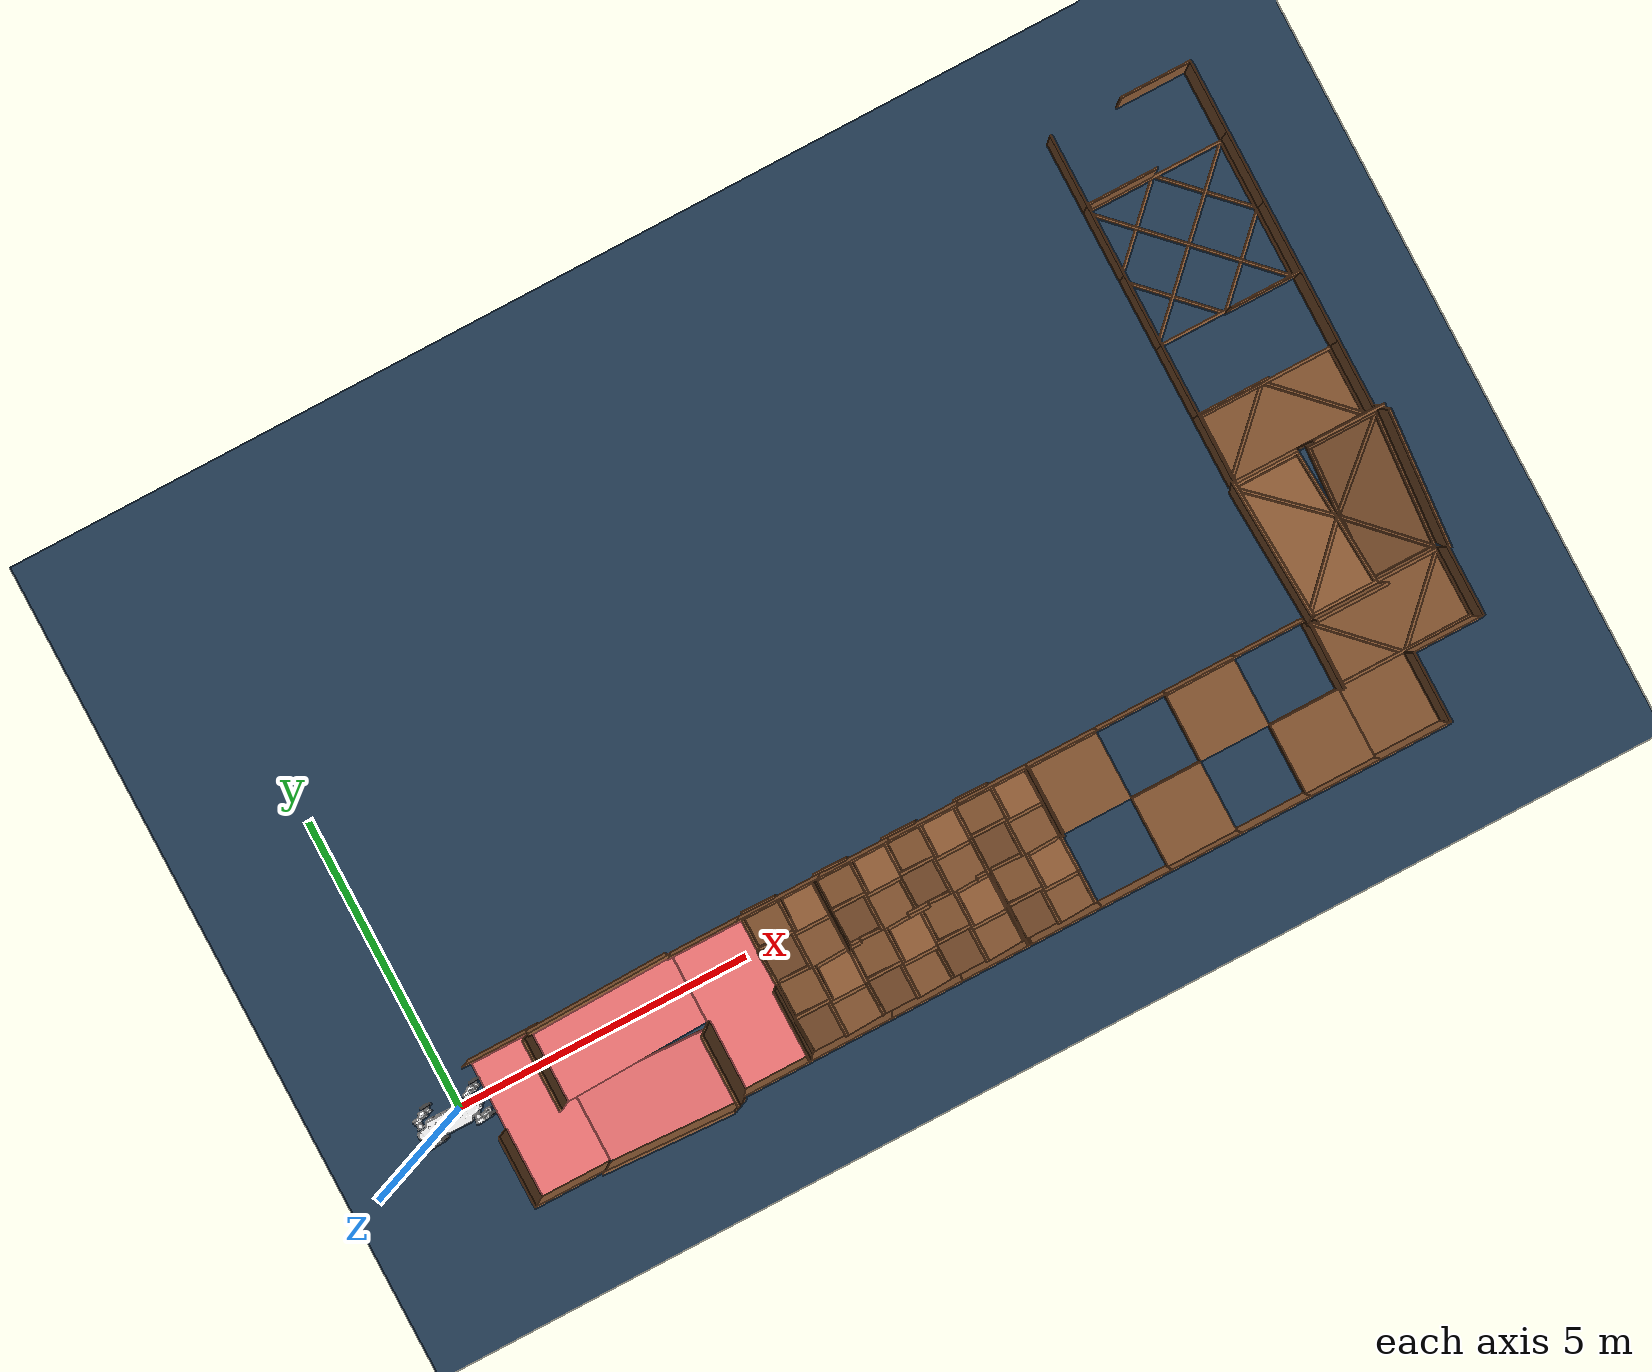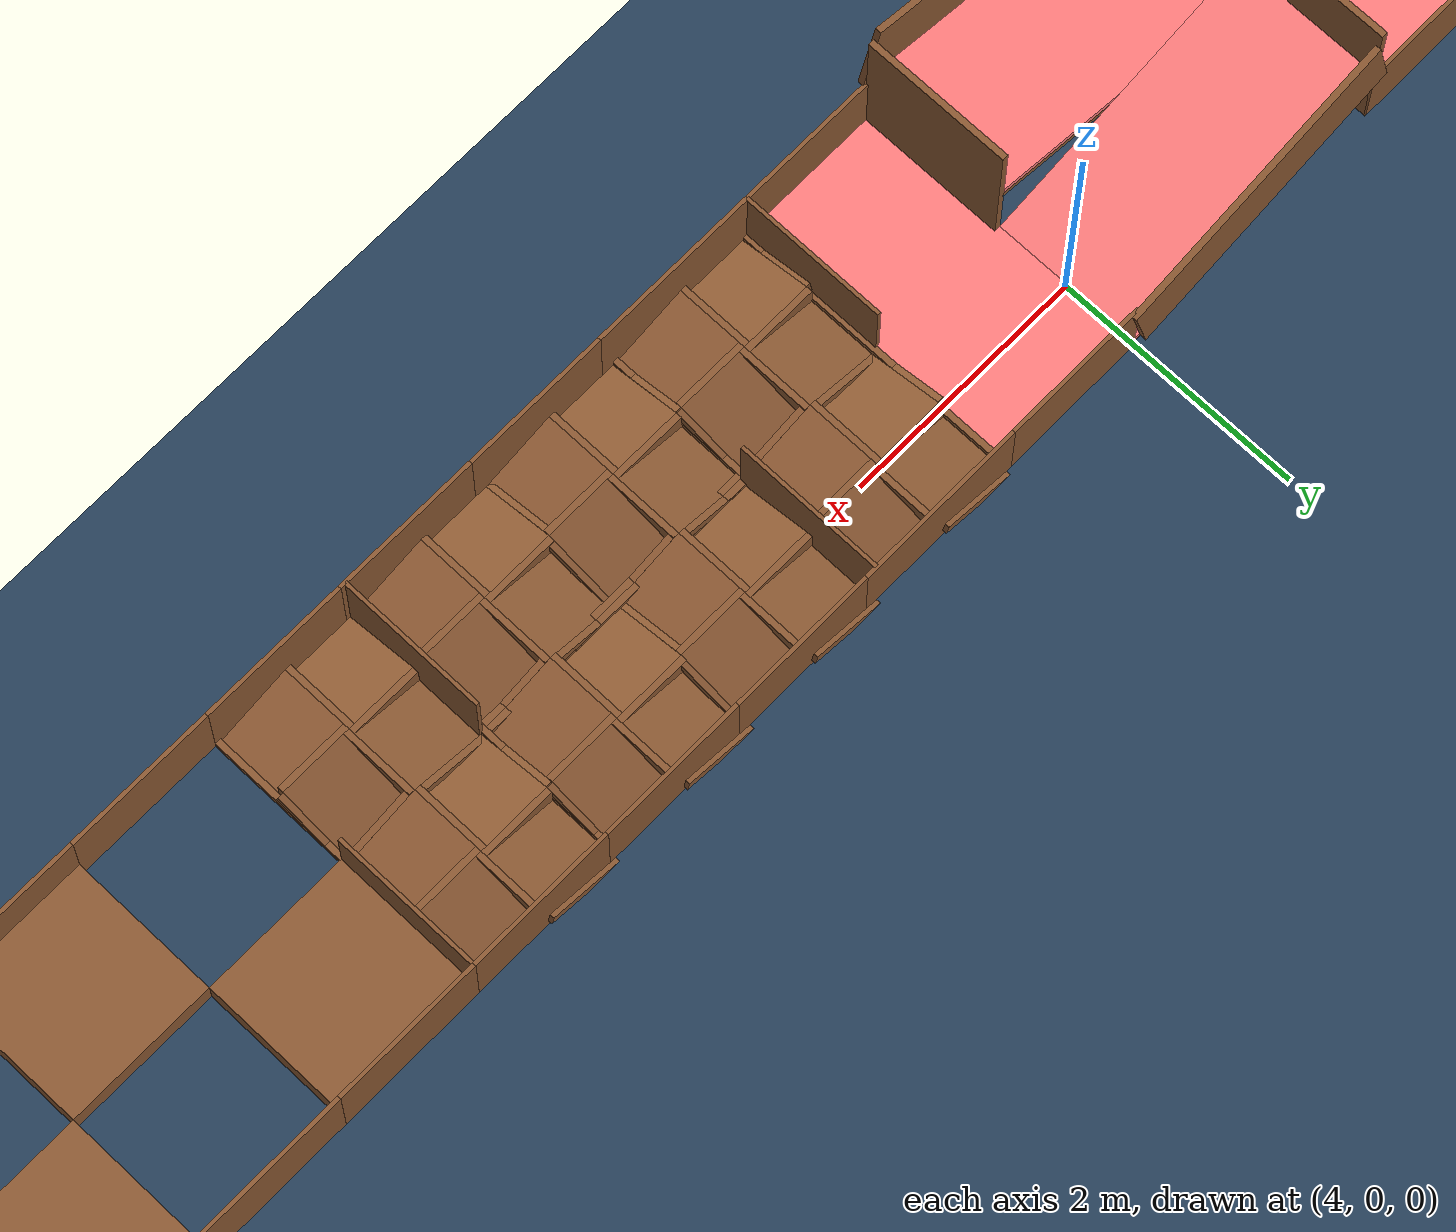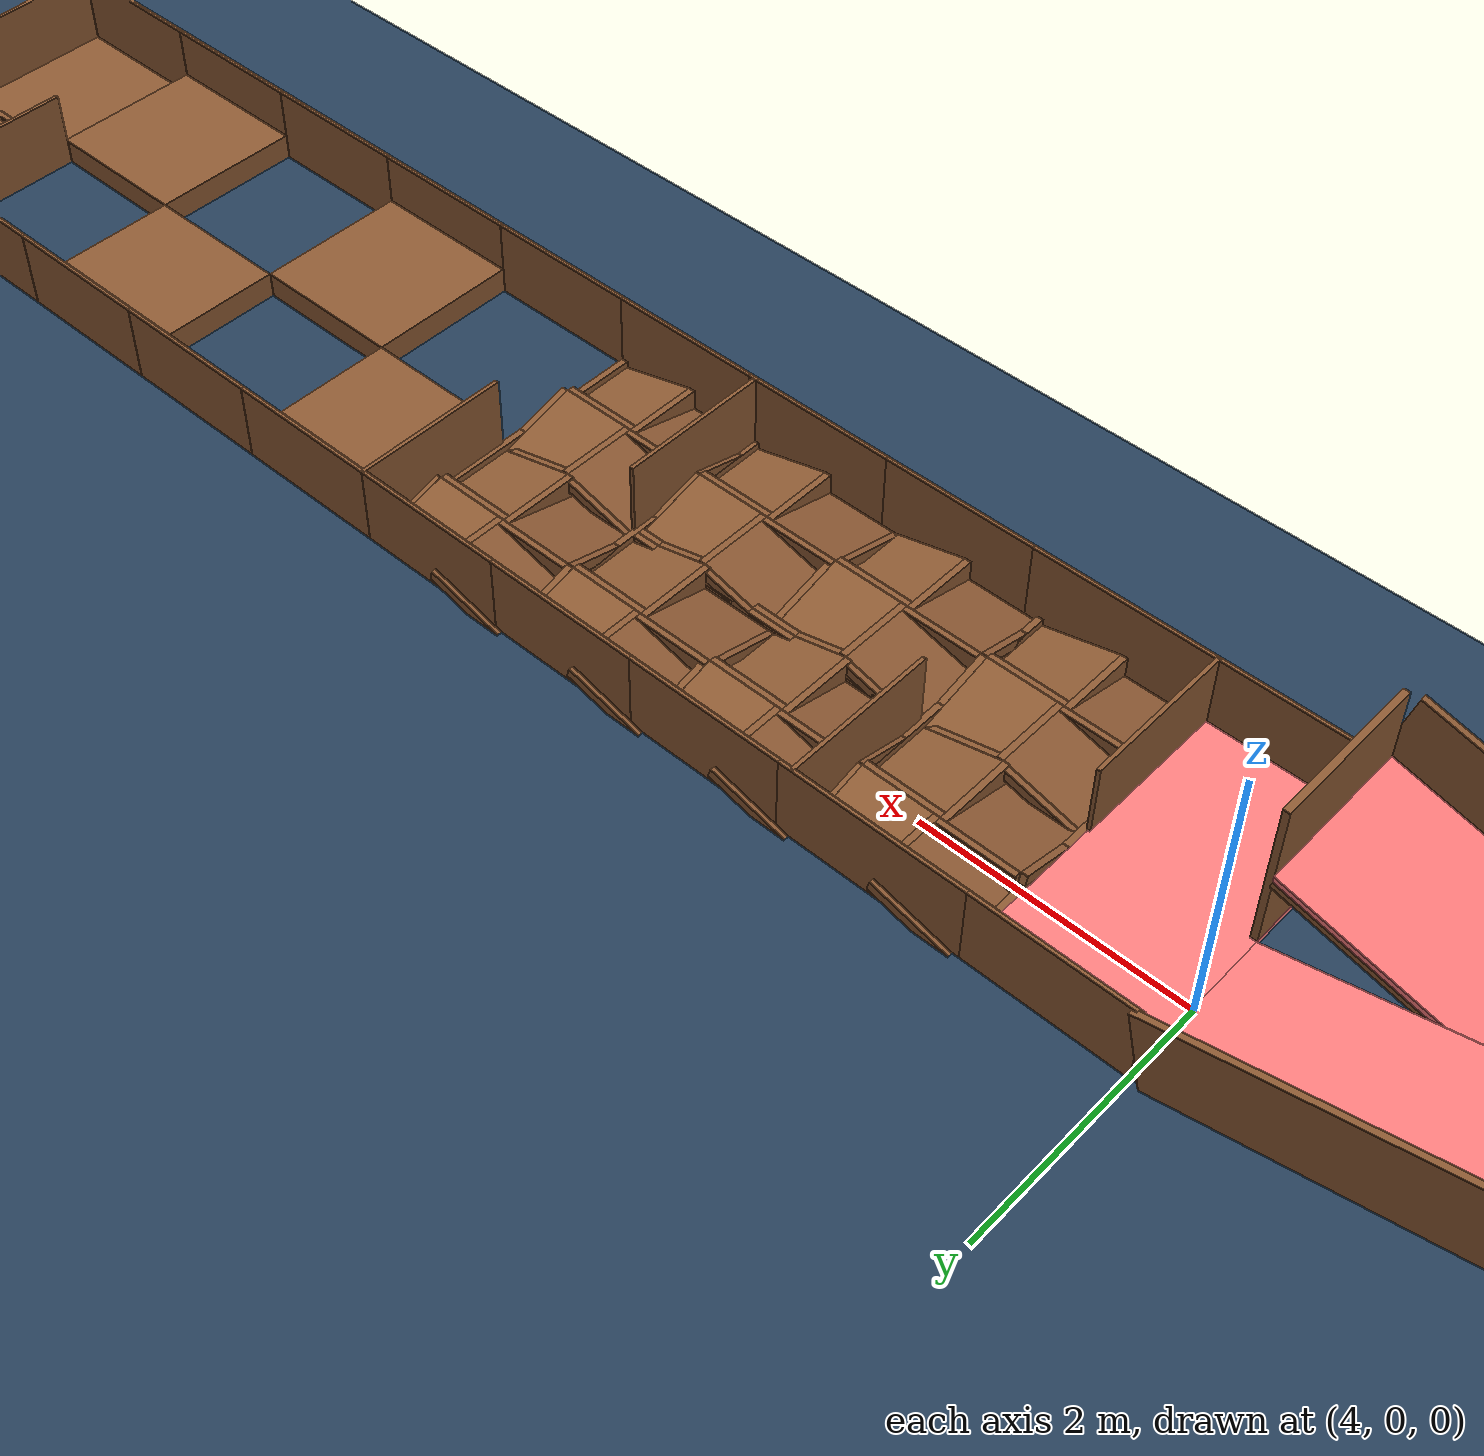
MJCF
<mujoco model="go2 scene">
  <include file="m20_big.xml"/>

  <statistic center="0 0 0.1" extent="0.8" />

  <visual>
    <headlight diffuse="0.6 0.6 0.6" ambient="0.3 0.3 0.3" specular="0 0 0" />
    <rgba haze="0.15 0.25 0.35 1" />
    <global azimuth="-130" elevation="-20" />
  </visual>

  <asset>
    <texture type="skybox" builtin="gradient" rgb1="0.3 0.5 0.7" rgb2="0 0 0" width="512" height="3072" />
    <texture type="2d" name="groundplane" builtin="checker" mark="edge" rgb1="0.2 0.3 0.4" rgb2="0.1 0.2 0.3" markrgb="0.8 0.8 0.8" width="300" height="300" />
    <material name="groundplane" texture="groundplane" texuniform="true" texrepeat="5 5" reflectance="0.0" />
  <texture name="wood_tex" type="2d" builtin="flat" rgb1="0.55 0.35 0.2" width="512" height="512" /><material name="wood_mat" texture="wood_tex" specular="0.2" shininess="0.1" rgba="1 1 1 1" /><texture name="sponge_tex" type="2d" builtin="flat" rgb1="1.0 0.7 0.7" width="512" height="512" /><material name="mat_sponge" texture="sponge_tex" specular="0.1" shininess="0.1" rgba="1 0.7 0.7 1" /></asset>

  <worldbody>
    <light pos="0 0 1.5" dir="0 0 -1" directional="true" />
    <geom name="floor" size="0 0 0.05" type="plane" material="groundplane" />
  <geom pos="2.833740429450787 2.220446049250313e-16 0.27579632720971" type="box" size="1.1981652640600127 0.6 0.025" quat="6.074277307224726e-17 0.12620041281310998 -7.727546580132487e-18 0.9920047660197004" material="wood_mat" friction="0.5 0.005 0.0001" /><geom pos="1.6550000000000002 2.220446049250313e-16 0.6" type="box" size="0.025 0.6 0.6" quat="6.123233995736766e-17 0.0 0.0 1.0" material="wood_mat" friction="0.5 0.005 0.0001" /><geom pos="2.833740429450787 0.6250000000000002 0.60079632720971" type="box" size="1.1981652640600127 0.025 0.3" quat="6.074277307224726e-17 0.12620041281310998 -7.727546580132487e-18 0.9920047660197004" material="wood_mat" friction="0.5 0.005 0.0001" /><geom pos="2.846259570549213 -1.2 0.27579632720971" type="box" size="1.1981652640600127 0.6 0.025" quat="0.9920047660197004 0.0 -0.12620041281310998 0.0" material="wood_mat" friction="0.5 0.005 0.0001" /><geom pos="4.025 -1.2 0.6" type="box" size="0.025 0.6 0.6" quat="1.0 0.0 0.0 0.0" material="wood_mat" friction="0.5 0.005 0.0001" /><geom pos="2.846259570549213 -1.825 0.60079632720971" type="box" size="1.1981652640600127 0.025 0.3" quat="0.9920047660197004 0.0 -0.12620041281310998 0.0" material="wood_mat" friction="0.5 0.005 0.0001" /><geom pos="4.6 -1.7999999999999998 0.3" type="box" size="0.6 0.3 0.015" quat="0.7071067811865476 0.7071067811865476 0.0 0.0" material="wood_mat" friction="0.5 0.005 0.0001" /><geom pos="1.08 -1.7999999999999998 0.3" type="box" size="0.6 0.3 0.015" quat="0.7071067811865476 0.7071067811865476 0.0 0.0" material="wood_mat" friction="0.5 0.005 0.0001" /><geom pos="4.6 0.6000000000000001 0.3" type="box" size="0.6 0.3 0.015" quat="0.7071067811865476 0.7071067811865476 0.0 0.0" material="wood_mat" friction="0.5 0.005 0.0001" /><geom pos="1.08 0.6000000000000001 0.3" type="box" size="0.6 0.3 0.015" quat="0.7071067811865476 0.7071067811865476 0.0 0.0" material="wood_mat" friction="0.5 0.005 0.0001" /><geom pos="0.48 -1.2 0.3" type="box" size="0.3 0.6 0.015" quat="0.7071067811865476 0.0 0.7071067811865476 0.0" material="wood_mat" friction="0.5 0.005 0.0001" /><geom pos="1.08 -0.6 0.025" type="box" size="0.6 1.2 0.025" quat="1.0 0.0 0.0 0.0" material="mat_sponge" solref="0.03 1" priority="1" solmix="1" friction="1.2 0.005 0.0001" /><geom pos="4.6 -0.6 0.025" type="box" size="0.6 1.2 0.025" quat="1.0 0.0 0.0 0.0" material="mat_sponge" solref="0.03 1" priority="1" solmix="1" friction="1.2 0.005 0.0001" /><geom pos="2.833740429450787 2.220446049250313e-16 0.32579632720970997" type="box" size="1.1981652640600127 0.6 0.025" quat="6.074277307224726e-17 0.12620041281310998 -7.727546580132487e-18 0.9920047660197004" material="mat_sponge" solref="0.03 1" priority="1" solmix="1" friction="1.2 0.005 0.0001" /><geom pos="2.846259570549213 -1.2 0.32579632720970997" type="box" size="1.1981652640600127 0.6 0.025" quat="0.9920047660197004 0.0 -0.12620041281310998 0.0" material="mat_sponge" solref="0.03 1" priority="1" solmix="1" friction="1.2 0.005 0.0001" /><geom pos="5.225 -0.6 0.0" type="box" size="1.2 0.025 0.05" quat="0.7071067811865476 0.0 0.0 0.7071067811865476" material="wood_mat" friction="0.5 0.005 0.0001" /><geom pos="5.55 -1.4934084623528479 0.05788461836407774" type="box" size="0.311004823113726 0.3 0.025" quat="0.7008236699478855 0.09405415270352165 -0.09405415270352165 0.7008236699478855" material="wood_mat" friction="0.5 0.005 0.0001" /><geom pos="5.55 -1.1749999999999998 0.082" type="box" size="0.025 0.3 0.082" quat="0.7071067811865476 0.0 0.0 0.7071067811865476" material="wood_mat" friction="0.5 0.005 0.0001" /><geom pos="5.875 -1.4934084623528479 0.04188461836407773" type="box" size="0.311004823113726 0.025 0.041" quat="0.7008236699478855 0.09405415270352165 -0.09405415270352165 0.7008236699478855" material="wood_mat" friction="0.5 0.005 0.0001" /><geom pos="5.225 -1.4934084623528479 0.04188461836407773" type="box" size="0.311004823113726 0.025 0.041" quat="0.7008236699478855 0.09405415270352165 -0.09405415270352165 0.7008236699478855" material="wood_mat" friction="0.5 0.005 0.0001" /><geom pos="5.556591537647153 -0.8999999999999999 0.05788461836407774" type="box" size="0.311004823113726 0.3 0.025" quat="0.9911143388723852 0.0 -0.1330126583508304 0.0" material="wood_mat" friction="0.5 0.005 0.0001" /><geom pos="5.875 -0.8999999999999999 0.082" type="box" size="0.025 0.3 0.082" quat="1.0 0.0 0.0 0.0" material="wood_mat" friction="0.5 0.005 0.0001" /><geom pos="5.556591537647153 -1.225 0.04188461836407773" type="box" size="0.311004823113726 0.025 0.041" quat="0.9911143388723852 0.0 -0.1330126583508304 0.0" material="wood_mat" friction="0.5 0.005 0.0001" /><geom pos="5.556591537647153 -0.575 0.04188461836407773" type="box" size="0.311004823113726 0.025 0.041" quat="0.9911143388723852 0.0 -0.1330126583508304 0.0" material="wood_mat" friction="0.5 0.005 0.0001" /><geom pos="6.143408462352848 -1.5 0.05788461836407774" type="box" size="0.311004823113726 0.3 0.025" quat="6.068825013445559e-17 0.1330126583508304 -8.144676314771245e-18 0.9911143388723852" material="wood_mat" friction="0.5 0.005 0.0001" /><geom pos="5.825 -1.5 0.082" type="box" size="0.025 0.3 0.082" quat="6.123233995736766e-17 0.0 0.0 1.0" material="wood_mat" friction="0.5 0.005 0.0001" /><geom pos="6.143408462352848 -1.1749999999999998 0.04188461836407773" type="box" size="0.311004823113726 0.025 0.041" quat="6.068825013445559e-17 0.1330126583508304 -8.144676314771245e-18 0.9911143388723852" material="wood_mat" friction="0.5 0.005 0.0001" /><geom pos="6.143408462352848 -1.825 0.04188461836407773" type="box" size="0.311004823113726 0.025 0.041" quat="6.068825013445559e-17 0.1330126583508304 -8.144676314771245e-18 0.9911143388723852" material="wood_mat" friction="0.5 0.005 0.0001" /><geom pos="6.15 -0.9065915376471521 0.05788461836407774" type="box" size="0.311004823113726 0.3 0.025" quat="-0.7008236699478854 0.09405415270352165 0.09405415270352163 0.7008236699478855" material="wood_mat" friction="0.5 0.005 0.0001" /><geom pos="6.15 -1.225 0.082" type="box" size="0.025 0.3 0.082" quat="-0.7071067811865475 -0.0 0.0 0.7071067811865476" material="wood_mat" friction="0.5 0.005 0.0001" /><geom pos="5.824999999999999 -0.9065915376471521 0.04188461836407773" type="box" size="0.311004823113726 0.025 0.041" quat="-0.7008236699478854 0.09405415270352165 0.09405415270352163 0.7008236699478855" material="wood_mat" friction="0.5 0.005 0.0001" /><geom pos="6.475 -0.9065915376471521 0.04188461836407773" type="box" size="0.311004823113726 0.025 0.041" quat="-0.7008236699478854 0.09405415270352165 0.09405415270352163 0.7008236699478855" material="wood_mat" friction="0.5 0.005 0.0001" /><geom pos="5.55 -0.2934084623528479 0.05788461836407774" type="box" size="0.311004823113726 0.3 0.025" quat="0.7008236699478855 0.09405415270352165 -0.09405415270352165 0.7008236699478855" material="wood_mat" friction="0.5 0.005 0.0001" /><geom pos="5.55 0.025000000000000133 0.082" type="box" size="0.025 0.3 0.082" quat="0.7071067811865476 0.0 0.0 0.7071067811865476" material="wood_mat" friction="0.5 0.005 0.0001" /><geom pos="5.875 -0.2934084623528479 0.04188461836407773" type="box" size="0.311004823113726 0.025 0.041" quat="0.7008236699478855 0.09405415270352165 -0.09405415270352165 0.7008236699478855" material="wood_mat" friction="0.5 0.005 0.0001" /><geom pos="5.225 -0.2934084623528479 0.04188461836407773" type="box" size="0.311004823113726 0.025 0.041" quat="0.7008236699478855 0.09405415270352165 -0.09405415270352165 0.7008236699478855" material="wood_mat" friction="0.5 0.005 0.0001" /><geom pos="5.556591537647153 0.30000000000000004 0.05788461836407774" type="box" size="0.311004823113726 0.3 0.025" quat="0.9911143388723852 0.0 -0.1330126583508304 0.0" material="wood_mat" friction="0.5 0.005 0.0001" /><geom pos="5.875 0.30000000000000004 0.082" type="box" size="0.025 0.3 0.082" quat="1.0 0.0 0.0 0.0" material="wood_mat" friction="0.5 0.005 0.0001" /><geom pos="5.556591537647153 -0.02499999999999991 0.04188461836407773" type="box" size="0.311004823113726 0.025 0.041" quat="0.9911143388723852 0.0 -0.1330126583508304 0.0" material="wood_mat" friction="0.5 0.005 0.0001" /><geom pos="5.556591537647153 0.625 0.04188461836407773" type="box" size="0.311004823113726 0.025 0.041" quat="0.9911143388723852 0.0 -0.1330126583508304 0.0" material="wood_mat" friction="0.5 0.005 0.0001" /><geom pos="6.143408462352848 -0.30000000000000004 0.05788461836407774" type="box" size="0.311004823113726 0.3 0.025" quat="6.068825013445559e-17 0.1330126583508304 -8.144676314771245e-18 0.9911143388723852" material="wood_mat" friction="0.5 0.005 0.0001" /><geom pos="5.825 -0.29999999999999993 0.082" type="box" size="0.025 0.3 0.082" quat="6.123233995736766e-17 0.0 0.0 1.0" material="wood_mat" friction="0.5 0.005 0.0001" /><geom pos="6.143408462352848 0.025000000000000133 0.04188461836407773" type="box" size="0.311004823113726 0.025 0.041" quat="6.068825013445559e-17 0.1330126583508304 -8.144676314771245e-18 0.9911143388723852" material="wood_mat" friction="0.5 0.005 0.0001" /><geom pos="6.143408462352848 -0.625 0.04188461836407773" type="box" size="0.311004823113726 0.025 0.041" quat="6.068825013445559e-17 0.1330126583508304 -8.144676314771245e-18 0.9911143388723852" material="wood_mat" friction="0.5 0.005 0.0001" /><geom pos="6.15 0.2934084623528477 0.05788461836407774" type="box" size="0.311004823113726 0.3 0.025" quat="-0.7008236699478854 0.09405415270352165 0.09405415270352163 0.7008236699478855" material="wood_mat" friction="0.5 0.005 0.0001" /><geom pos="6.15 -0.025000000000000133 0.082" type="box" size="0.025 0.3 0.082" quat="-0.7071067811865475 -0.0 0.0 0.7071067811865476" material="wood_mat" friction="0.5 0.005 0.0001" /><geom pos="5.824999999999999 0.2934084623528479 0.04188461836407773" type="box" size="0.311004823113726 0.025 0.041" quat="-0.7008236699478854 0.09405415270352165 0.09405415270352163 0.7008236699478855" material="wood_mat" friction="0.5 0.005 0.0001" /><geom pos="6.475 0.2934084623528477 0.04188461836407773" type="box" size="0.311004823113726 0.025 0.041" quat="-0.7008236699478854 0.09405415270352165 0.09405415270352163 0.7008236699478855" material="wood_mat" friction="0.5 0.005 0.0001" /><geom pos="6.475 -0.6 0.0" type="box" size="1.2 0.025 0.05" quat="0.7071067811865476 0.0 0.0 0.7071067811865476" material="wood_mat" friction="0.5 0.005 0.0001" /><geom pos="6.800000000000001 -1.4934084623528479 0.05788461836407774" type="box" size="0.311004823113726 0.3 0.025" quat="0.7008236699478855 0.09405415270352165 -0.09405415270352165 0.7008236699478855" material="wood_mat" friction="0.5 0.005 0.0001" /><geom pos="6.800000000000001 -1.1749999999999998 0.082" type="box" size="0.025 0.3 0.082" quat="0.7071067811865476 0.0 0.0 0.7071067811865476" material="wood_mat" friction="0.5 0.005 0.0001" /><geom pos="7.125 -1.4934084623528479 0.04188461836407773" type="box" size="0.311004823113726 0.025 0.041" quat="0.7008236699478855 0.09405415270352165 -0.09405415270352165 0.7008236699478855" material="wood_mat" friction="0.5 0.005 0.0001" /><geom pos="6.475 -1.4934084623528479 0.04188461836407773" type="box" size="0.311004823113726 0.025 0.041" quat="0.7008236699478855 0.09405415270352165 -0.09405415270352165 0.7008236699478855" material="wood_mat" friction="0.5 0.005 0.0001" /><geom pos="6.806591537647153 -0.8999999999999999 0.05788461836407774" type="box" size="0.311004823113726 0.3 0.025" quat="0.9911143388723852 0.0 -0.1330126583508304 0.0" material="wood_mat" friction="0.5 0.005 0.0001" /><geom pos="7.125 -0.8999999999999999 0.082" type="box" size="0.025 0.3 0.082" quat="1.0 0.0 0.0 0.0" material="wood_mat" friction="0.5 0.005 0.0001" /><geom pos="6.806591537647153 -1.225 0.04188461836407773" type="box" size="0.311004823113726 0.025 0.041" quat="0.9911143388723852 0.0 -0.1330126583508304 0.0" material="wood_mat" friction="0.5 0.005 0.0001" /><geom pos="6.806591537647153 -0.575 0.04188461836407773" type="box" size="0.311004823113726 0.025 0.041" quat="0.9911143388723852 0.0 -0.1330126583508304 0.0" material="wood_mat" friction="0.5 0.005 0.0001" /><geom pos="7.393408462352848 -1.5 0.05788461836407774" type="box" size="0.311004823113726 0.3 0.025" quat="6.068825013445559e-17 0.1330126583508304 -8.144676314771245e-18 0.9911143388723852" material="wood_mat" friction="0.5 0.005 0.0001" /><geom pos="7.075 -1.5 0.082" type="box" size="0.025 0.3 0.082" quat="6.123233995736766e-17 0.0 0.0 1.0" material="wood_mat" friction="0.5 0.005 0.0001" /><geom pos="7.393408462352848 -1.1749999999999998 0.04188461836407773" type="box" size="0.311004823113726 0.025 0.041" quat="6.068825013445559e-17 0.1330126583508304 -8.144676314771245e-18 0.9911143388723852" material="wood_mat" friction="0.5 0.005 0.0001" /><geom pos="7.393408462352848 -1.825 0.04188461836407773" type="box" size="0.311004823113726 0.025 0.041" quat="6.068825013445559e-17 0.1330126583508304 -8.144676314771245e-18 0.9911143388723852" material="wood_mat" friction="0.5 0.005 0.0001" /><geom pos="7.4 -0.9065915376471521 0.05788461836407774" type="box" size="0.311004823113726 0.3 0.025" quat="-0.7008236699478854 0.09405415270352165 0.09405415270352163 0.7008236699478855" material="wood_mat" friction="0.5 0.005 0.0001" /><geom pos="7.4 -1.225 0.082" type="box" size="0.025 0.3 0.082" quat="-0.7071067811865475 -0.0 0.0 0.7071067811865476" material="wood_mat" friction="0.5 0.005 0.0001" /><geom pos="7.074999999999999 -0.9065915376471521 0.04188461836407773" type="box" size="0.311004823113726 0.025 0.041" quat="-0.7008236699478854 0.09405415270352165 0.09405415270352163 0.7008236699478855" material="wood_mat" friction="0.5 0.005 0.0001" /><geom pos="7.725 -0.9065915376471521 0.04188461836407773" type="box" size="0.311004823113726 0.025 0.041" quat="-0.7008236699478854 0.09405415270352165 0.09405415270352163 0.7008236699478855" material="wood_mat" friction="0.5 0.005 0.0001" /><geom pos="6.800000000000001 -0.2934084623528479 0.05788461836407774" type="box" size="0.311004823113726 0.3 0.025" quat="0.7008236699478855 0.09405415270352165 -0.09405415270352165 0.7008236699478855" material="wood_mat" friction="0.5 0.005 0.0001" /><geom pos="6.800000000000001 0.025000000000000133 0.082" type="box" size="0.025 0.3 0.082" quat="0.7071067811865476 0.0 0.0 0.7071067811865476" material="wood_mat" friction="0.5 0.005 0.0001" /><geom pos="7.125 -0.2934084623528479 0.04188461836407773" type="box" size="0.311004823113726 0.025 0.041" quat="0.7008236699478855 0.09405415270352165 -0.09405415270352165 0.7008236699478855" material="wood_mat" friction="0.5 0.005 0.0001" /><geom pos="6.475 -0.2934084623528479 0.04188461836407773" type="box" size="0.311004823113726 0.025 0.041" quat="0.7008236699478855 0.09405415270352165 -0.09405415270352165 0.7008236699478855" material="wood_mat" friction="0.5 0.005 0.0001" /><geom pos="6.806591537647153 0.30000000000000004 0.05788461836407774" type="box" size="0.311004823113726 0.3 0.025" quat="0.9911143388723852 0.0 -0.1330126583508304 0.0" material="wood_mat" friction="0.5 0.005 0.0001" /><geom pos="7.125 0.30000000000000004 0.082" type="box" size="0.025 0.3 0.082" quat="1.0 0.0 0.0 0.0" material="wood_mat" friction="0.5 0.005 0.0001" /><geom pos="6.806591537647153 -0.02499999999999991 0.04188461836407773" type="box" size="0.311004823113726 0.025 0.041" quat="0.9911143388723852 0.0 -0.1330126583508304 0.0" material="wood_mat" friction="0.5 0.005 0.0001" /><geom pos="6.806591537647153 0.625 0.04188461836407773" type="box" size="0.311004823113726 0.025 0.041" quat="0.9911143388723852 0.0 -0.1330126583508304 0.0" material="wood_mat" friction="0.5 0.005 0.0001" /><geom pos="7.393408462352848 -0.30000000000000004 0.05788461836407774" type="box" size="0.311004823113726 0.3 0.025" quat="6.068825013445559e-17 0.1330126583508304 -8.144676314771245e-18 0.9911143388723852" material="wood_mat" friction="0.5 0.005 0.0001" /><geom pos="7.075 -0.29999999999999993 0.082" type="box" size="0.025 0.3 0.082" quat="6.123233995736766e-17 0.0 0.0 1.0" material="wood_mat" friction="0.5 0.005 0.0001" /><geom pos="7.393408462352848 0.025000000000000133 0.04188461836407773" type="box" size="0.311004823113726 0.025 0.041" quat="6.068825013445559e-17 0.1330126583508304 -8.144676314771245e-18 0.9911143388723852" material="wood_mat" friction="0.5 0.005 0.0001" /><geom pos="7.393408462352848 -0.625 0.04188461836407773" type="box" size="0.311004823113726 0.025 0.041" quat="6.068825013445559e-17 0.1330126583508304 -8.144676314771245e-18 0.9911143388723852" material="wood_mat" friction="0.5 0.005 0.0001" /><geom pos="7.4 0.2934084623528477 0.05788461836407774" type="box" size="0.311004823113726 0.3 0.025" quat="-0.7008236699478854 0.09405415270352165 0.09405415270352163 0.7008236699478855" material="wood_mat" friction="0.5 0.005 0.0001" /><geom pos="7.4 -0.025000000000000133 0.082" type="box" size="0.025 0.3 0.082" quat="-0.7071067811865475 -0.0 0.0 0.7071067811865476" material="wood_mat" friction="0.5 0.005 0.0001" /><geom pos="7.074999999999999 0.2934084623528479 0.04188461836407773" type="box" size="0.311004823113726 0.025 0.041" quat="-0.7008236699478854 0.09405415270352165 0.09405415270352163 0.7008236699478855" material="wood_mat" friction="0.5 0.005 0.0001" /><geom pos="7.725 0.2934084623528477 0.04188461836407773" type="box" size="0.311004823113726 0.025 0.041" quat="-0.7008236699478854 0.09405415270352165 0.09405415270352163 0.7008236699478855" material="wood_mat" friction="0.5 0.005 0.0001" /><geom pos="8.0 -1.4934084623528479 0.05788461836407774" type="box" size="0.311004823113726 0.3 0.025" quat="0.7008236699478855 0.09405415270352165 -0.09405415270352165 0.7008236699478855" material="wood_mat" friction="0.5 0.005 0.0001" /><geom pos="8.0 -1.1749999999999998 0.082" type="box" size="0.025 0.3 0.082" quat="0.7071067811865476 0.0 0.0 0.7071067811865476" material="wood_mat" friction="0.5 0.005 0.0001" /><geom pos="8.325 -1.4934084623528479 0.04188461836407773" type="box" size="0.311004823113726 0.025 0.041" quat="0.7008236699478855 0.09405415270352165 -0.09405415270352165 0.7008236699478855" material="wood_mat" friction="0.5 0.005 0.0001" /><geom pos="7.675 -1.4934084623528479 0.04188461836407773" type="box" size="0.311004823113726 0.025 0.041" quat="0.7008236699478855 0.09405415270352165 -0.09405415270352165 0.7008236699478855" material="wood_mat" friction="0.5 0.005 0.0001" /><geom pos="8.006591537647152 -0.8999999999999999 0.05788461836407774" type="box" size="0.311004823113726 0.3 0.025" quat="0.9911143388723852 0.0 -0.1330126583508304 0.0" material="wood_mat" friction="0.5 0.005 0.0001" /><geom pos="8.325 -0.8999999999999999 0.082" type="box" size="0.025 0.3 0.082" quat="1.0 0.0 0.0 0.0" material="wood_mat" friction="0.5 0.005 0.0001" /><geom pos="8.006591537647152 -1.225 0.04188461836407773" type="box" size="0.311004823113726 0.025 0.041" quat="0.9911143388723852 0.0 -0.1330126583508304 0.0" material="wood_mat" friction="0.5 0.005 0.0001" /><geom pos="8.006591537647152 -0.575 0.04188461836407773" type="box" size="0.311004823113726 0.025 0.041" quat="0.9911143388723852 0.0 -0.1330126583508304 0.0" material="wood_mat" friction="0.5 0.005 0.0001" /><geom pos="8.593408462352848 -1.5 0.05788461836407774" type="box" size="0.311004823113726 0.3 0.025" quat="6.068825013445559e-17 0.1330126583508304 -8.144676314771245e-18 0.9911143388723852" material="wood_mat" friction="0.5 0.005 0.0001" /><geom pos="8.274999999999999 -1.5 0.082" type="box" size="0.025 0.3 0.082" quat="6.123233995736766e-17 0.0 0.0 1.0" material="wood_mat" friction="0.5 0.005 0.0001" /><geom pos="8.593408462352848 -1.1749999999999998 0.04188461836407773" type="box" size="0.311004823113726 0.025 0.041" quat="6.068825013445559e-17 0.1330126583508304 -8.144676314771245e-18 0.9911143388723852" material="wood_mat" friction="0.5 0.005 0.0001" /><geom pos="8.593408462352848 -1.825 0.04188461836407773" type="box" size="0.311004823113726 0.025 0.041" quat="6.068825013445559e-17 0.1330126583508304 -8.144676314771245e-18 0.9911143388723852" material="wood_mat" friction="0.5 0.005 0.0001" /><geom pos="8.6 -0.9065915376471521 0.05788461836407774" type="box" size="0.311004823113726 0.3 0.025" quat="-0.7008236699478854 0.09405415270352165 0.09405415270352163 0.7008236699478855" material="wood_mat" friction="0.5 0.005 0.0001" /><geom pos="8.6 -1.225 0.082" type="box" size="0.025 0.3 0.082" quat="-0.7071067811865475 -0.0 0.0 0.7071067811865476" material="wood_mat" friction="0.5 0.005 0.0001" /><geom pos="8.274999999999999 -0.9065915376471521 0.04188461836407773" type="box" size="0.311004823113726 0.025 0.041" quat="-0.7008236699478854 0.09405415270352165 0.09405415270352163 0.7008236699478855" material="wood_mat" friction="0.5 0.005 0.0001" /><geom pos="8.925 -0.9065915376471521 0.04188461836407773" type="box" size="0.311004823113726 0.025 0.041" quat="-0.7008236699478854 0.09405415270352165 0.09405415270352163 0.7008236699478855" material="wood_mat" friction="0.5 0.005 0.0001" /><geom pos="8.0 -0.2934084623528479 0.05788461836407774" type="box" size="0.311004823113726 0.3 0.025" quat="0.7008236699478855 0.09405415270352165 -0.09405415270352165 0.7008236699478855" material="wood_mat" friction="0.5 0.005 0.0001" /><geom pos="8.0 0.025000000000000133 0.082" type="box" size="0.025 0.3 0.082" quat="0.7071067811865476 0.0 0.0 0.7071067811865476" material="wood_mat" friction="0.5 0.005 0.0001" /><geom pos="8.325 -0.2934084623528479 0.04188461836407773" type="box" size="0.311004823113726 0.025 0.041" quat="0.7008236699478855 0.09405415270352165 -0.09405415270352165 0.7008236699478855" material="wood_mat" friction="0.5 0.005 0.0001" /><geom pos="7.675 -0.2934084623528479 0.04188461836407773" type="box" size="0.311004823113726 0.025 0.041" quat="0.7008236699478855 0.09405415270352165 -0.09405415270352165 0.7008236699478855" material="wood_mat" friction="0.5 0.005 0.0001" /><geom pos="8.006591537647152 0.30000000000000004 0.05788461836407774" type="box" size="0.311004823113726 0.3 0.025" quat="0.9911143388723852 0.0 -0.1330126583508304 0.0" material="wood_mat" friction="0.5 0.005 0.0001" /><geom pos="8.325 0.30000000000000004 0.082" type="box" size="0.025 0.3 0.082" quat="1.0 0.0 0.0 0.0" material="wood_mat" friction="0.5 0.005 0.0001" /><geom pos="8.006591537647152 -0.02499999999999991 0.04188461836407773" type="box" size="0.311004823113726 0.025 0.041" quat="0.9911143388723852 0.0 -0.1330126583508304 0.0" material="wood_mat" friction="0.5 0.005 0.0001" /><geom pos="8.006591537647152 0.625 0.04188461836407773" type="box" size="0.311004823113726 0.025 0.041" quat="0.9911143388723852 0.0 -0.1330126583508304 0.0" material="wood_mat" friction="0.5 0.005 0.0001" /><geom pos="8.593408462352848 -0.30000000000000004 0.05788461836407774" type="box" size="0.311004823113726 0.3 0.025" quat="6.068825013445559e-17 0.1330126583508304 -8.144676314771245e-18 0.9911143388723852" material="wood_mat" friction="0.5 0.005 0.0001" /><geom pos="8.274999999999999 -0.29999999999999993 0.082" type="box" size="0.025 0.3 0.082" quat="6.123233995736766e-17 0.0 0.0 1.0" material="wood_mat" friction="0.5 0.005 0.0001" /><geom pos="8.593408462352848 0.025000000000000133 0.04188461836407773" type="box" size="0.311004823113726 0.025 0.041" quat="6.068825013445559e-17 0.1330126583508304 -8.144676314771245e-18 0.9911143388723852" material="wood_mat" friction="0.5 0.005 0.0001" /><geom pos="8.593408462352848 -0.625 0.04188461836407773" type="box" size="0.311004823113726 0.025 0.041" quat="6.068825013445559e-17 0.1330126583508304 -8.144676314771245e-18 0.9911143388723852" material="wood_mat" friction="0.5 0.005 0.0001" /><geom pos="8.6 0.2934084623528477 0.05788461836407774" type="box" size="0.311004823113726 0.3 0.025" quat="-0.7008236699478854 0.09405415270352165 0.09405415270352163 0.7008236699478855" material="wood_mat" friction="0.5 0.005 0.0001" /><geom pos="8.6 -0.025000000000000133 0.082" type="box" size="0.025 0.3 0.082" quat="-0.7071067811865475 -0.0 0.0 0.7071067811865476" material="wood_mat" friction="0.5 0.005 0.0001" /><geom pos="8.274999999999999 0.2934084623528479 0.04188461836407773" type="box" size="0.311004823113726 0.025 0.041" quat="-0.7008236699478854 0.09405415270352165 0.09405415270352163 0.7008236699478855" material="wood_mat" friction="0.5 0.005 0.0001" /><geom pos="8.925 0.2934084623528477 0.04188461836407773" type="box" size="0.311004823113726 0.025 0.041" quat="-0.7008236699478854 0.09405415270352165 0.09405415270352163 0.7008236699478855" material="wood_mat" friction="0.5 0.005 0.0001" /><geom pos="7.7 -0.625 0.0" type="box" size="1.2 0.025 0.05" quat="1.0 0.0 0.0 0.0" material="wood_mat" friction="0.5 0.005 0.0001" /><geom pos="7.7 -0.575 0.0" type="box" size="1.2 0.025 0.05" quat="1.0 0.0 0.0 0.0" material="wood_mat" friction="0.5 0.005 0.0001" /><geom pos="8.925 -0.6 0.0" type="box" size="1.2 0.025 0.05" quat="0.7071067811865476 0.0 0.0 0.7071067811865476" material="wood_mat" friction="0.5 0.005 0.0001" /><geom pos="9.25 -1.4934084623528479 0.05788461836407774" type="box" size="0.311004823113726 0.3 0.025" quat="0.7008236699478855 0.09405415270352165 -0.09405415270352165 0.7008236699478855" material="wood_mat" friction="0.5 0.005 0.0001" /><geom pos="9.25 -1.1749999999999998 0.082" type="box" size="0.025 0.3 0.082" quat="0.7071067811865476 0.0 0.0 0.7071067811865476" material="wood_mat" friction="0.5 0.005 0.0001" /><geom pos="9.575 -1.4934084623528479 0.04188461836407773" type="box" size="0.311004823113726 0.025 0.041" quat="0.7008236699478855 0.09405415270352165 -0.09405415270352165 0.7008236699478855" material="wood_mat" friction="0.5 0.005 0.0001" /><geom pos="8.925 -1.4934084623528479 0.04188461836407773" type="box" size="0.311004823113726 0.025 0.041" quat="0.7008236699478855 0.09405415270352165 -0.09405415270352165 0.7008236699478855" material="wood_mat" friction="0.5 0.005 0.0001" /><geom pos="9.256591537647152 -0.8999999999999999 0.05788461836407774" type="box" size="0.311004823113726 0.3 0.025" quat="0.9911143388723852 0.0 -0.1330126583508304 0.0" material="wood_mat" friction="0.5 0.005 0.0001" /><geom pos="9.575 -0.8999999999999999 0.082" type="box" size="0.025 0.3 0.082" quat="1.0 0.0 0.0 0.0" material="wood_mat" friction="0.5 0.005 0.0001" /><geom pos="9.256591537647152 -1.225 0.04188461836407773" type="box" size="0.311004823113726 0.025 0.041" quat="0.9911143388723852 0.0 -0.1330126583508304 0.0" material="wood_mat" friction="0.5 0.005 0.0001" /><geom pos="9.256591537647152 -0.575 0.04188461836407773" type="box" size="0.311004823113726 0.025 0.041" quat="0.9911143388723852 0.0 -0.1330126583508304 0.0" material="wood_mat" friction="0.5 0.005 0.0001" /><geom pos="9.843408462352848 -1.5 0.05788461836407774" type="box" size="0.311004823113726 0.3 0.025" quat="6.068825013445559e-17 0.1330126583508304 -8.144676314771245e-18 0.9911143388723852" material="wood_mat" friction="0.5 0.005 0.0001" /><geom pos="9.524999999999999 -1.5 0.082" type="box" size="0.025 0.3 0.082" quat="6.123233995736766e-17 0.0 0.0 1.0" material="wood_mat" friction="0.5 0.005 0.0001" /><geom pos="9.843408462352848 -1.1749999999999998 0.04188461836407773" type="box" size="0.311004823113726 0.025 0.041" quat="6.068825013445559e-17 0.1330126583508304 -8.144676314771245e-18 0.9911143388723852" material="wood_mat" friction="0.5 0.005 0.0001" /><geom pos="9.843408462352848 -1.825 0.04188461836407773" type="box" size="0.311004823113726 0.025 0.041" quat="6.068825013445559e-17 0.1330126583508304 -8.144676314771245e-18 0.9911143388723852" material="wood_mat" friction="0.5 0.005 0.0001" /><geom pos="9.85 -0.9065915376471521 0.05788461836407774" type="box" size="0.311004823113726 0.3 0.025" quat="-0.7008236699478854 0.09405415270352165 0.09405415270352163 0.7008236699478855" material="wood_mat" friction="0.5 0.005 0.0001" /><geom pos="9.85 -1.225 0.082" type="box" size="0.025 0.3 0.082" quat="-0.7071067811865475 -0.0 0.0 0.7071067811865476" material="wood_mat" friction="0.5 0.005 0.0001" /><geom pos="9.524999999999999 -0.9065915376471521 0.04188461836407773" type="box" size="0.311004823113726 0.025 0.041" quat="-0.7008236699478854 0.09405415270352165 0.09405415270352163 0.7008236699478855" material="wood_mat" friction="0.5 0.005 0.0001" /><geom pos="10.175 -0.9065915376471521 0.04188461836407773" type="box" size="0.311004823113726 0.025 0.041" quat="-0.7008236699478854 0.09405415270352165 0.09405415270352163 0.7008236699478855" material="wood_mat" friction="0.5 0.005 0.0001" /><geom pos="9.25 -0.2934084623528479 0.05788461836407774" type="box" size="0.311004823113726 0.3 0.025" quat="0.7008236699478855 0.09405415270352165 -0.09405415270352165 0.7008236699478855" material="wood_mat" friction="0.5 0.005 0.0001" /><geom pos="9.25 0.025000000000000133 0.082" type="box" size="0.025 0.3 0.082" quat="0.7071067811865476 0.0 0.0 0.7071067811865476" material="wood_mat" friction="0.5 0.005 0.0001" /><geom pos="9.575 -0.2934084623528479 0.04188461836407773" type="box" size="0.311004823113726 0.025 0.041" quat="0.7008236699478855 0.09405415270352165 -0.09405415270352165 0.7008236699478855" material="wood_mat" friction="0.5 0.005 0.0001" /><geom pos="8.925 -0.2934084623528479 0.04188461836407773" type="box" size="0.311004823113726 0.025 0.041" quat="0.7008236699478855 0.09405415270352165 -0.09405415270352165 0.7008236699478855" material="wood_mat" friction="0.5 0.005 0.0001" /><geom pos="9.256591537647152 0.30000000000000004 0.05788461836407774" type="box" size="0.311004823113726 0.3 0.025" quat="0.9911143388723852 0.0 -0.1330126583508304 0.0" material="wood_mat" friction="0.5 0.005 0.0001" /><geom pos="9.575 0.30000000000000004 0.082" type="box" size="0.025 0.3 0.082" quat="1.0 0.0 0.0 0.0" material="wood_mat" friction="0.5 0.005 0.0001" /><geom pos="9.256591537647152 -0.02499999999999991 0.04188461836407773" type="box" size="0.311004823113726 0.025 0.041" quat="0.9911143388723852 0.0 -0.1330126583508304 0.0" material="wood_mat" friction="0.5 0.005 0.0001" /><geom pos="9.256591537647152 0.625 0.04188461836407773" type="box" size="0.311004823113726 0.025 0.041" quat="0.9911143388723852 0.0 -0.1330126583508304 0.0" material="wood_mat" friction="0.5 0.005 0.0001" /><geom pos="9.843408462352848 -0.30000000000000004 0.05788461836407774" type="box" size="0.311004823113726 0.3 0.025" quat="6.068825013445559e-17 0.1330126583508304 -8.144676314771245e-18 0.9911143388723852" material="wood_mat" friction="0.5 0.005 0.0001" /><geom pos="9.524999999999999 -0.29999999999999993 0.082" type="box" size="0.025 0.3 0.082" quat="6.123233995736766e-17 0.0 0.0 1.0" material="wood_mat" friction="0.5 0.005 0.0001" /><geom pos="9.843408462352848 0.025000000000000133 0.04188461836407773" type="box" size="0.311004823113726 0.025 0.041" quat="6.068825013445559e-17 0.1330126583508304 -8.144676314771245e-18 0.9911143388723852" material="wood_mat" friction="0.5 0.005 0.0001" /><geom pos="9.843408462352848 -0.625 0.04188461836407773" type="box" size="0.311004823113726 0.025 0.041" quat="6.068825013445559e-17 0.1330126583508304 -8.144676314771245e-18 0.9911143388723852" material="wood_mat" friction="0.5 0.005 0.0001" /><geom pos="9.85 0.2934084623528477 0.05788461836407774" type="box" size="0.311004823113726 0.3 0.025" quat="-0.7008236699478854 0.09405415270352165 0.09405415270352163 0.7008236699478855" material="wood_mat" friction="0.5 0.005 0.0001" /><geom pos="9.85 -0.025000000000000133 0.082" type="box" size="0.025 0.3 0.082" quat="-0.7071067811865475 -0.0 0.0 0.7071067811865476" material="wood_mat" friction="0.5 0.005 0.0001" /><geom pos="9.524999999999999 0.2934084623528479 0.04188461836407773" type="box" size="0.311004823113726 0.025 0.041" quat="-0.7008236699478854 0.09405415270352165 0.09405415270352163 0.7008236699478855" material="wood_mat" friction="0.5 0.005 0.0001" /><geom pos="10.175 0.2934084623528477 0.04188461836407773" type="box" size="0.311004823113726 0.025 0.041" quat="-0.7008236699478854 0.09405415270352165 0.09405415270352163 0.7008236699478855" material="wood_mat" friction="0.5 0.005 0.0001" /><geom pos="10.175 -0.6 0.0" type="box" size="1.2 0.025 0.05" quat="0.7071067811865476 0.0 0.0 0.7071067811865476" material="wood_mat" friction="0.5 0.005 0.0001" /><geom pos="5.9 0.6000000000000001 0.3" type="box" size="0.7 0.3 0.015" quat="0.7071067811865476 0.7071067811865476 0.0 0.0" material="wood_mat" friction="0.5 0.005 0.0001" /><geom pos="7.2 0.6000000000000001 0.3" type="box" size="0.6 0.3 0.015" quat="0.7071067811865476 0.7071067811865476 0.0 0.0" material="wood_mat" friction="0.5 0.005 0.0001" /><geom pos="8.4 0.6000000000000001 0.3" type="box" size="0.6 0.3 0.015" quat="0.7071067811865476 0.7071067811865476 0.0 0.0" material="wood_mat" friction="0.5 0.005 0.0001" /><geom pos="9.6 0.6000000000000001 0.3" type="box" size="0.6 0.3 0.015" quat="0.7071067811865476 0.7071067811865476 0.0 0.0" material="wood_mat" friction="0.5 0.005 0.0001" /><geom pos="5.9 -1.7999999999999998 0.3" type="box" size="0.7 0.3 0.015" quat="0.7071067811865476 0.7071067811865476 0.0 0.0" material="wood_mat" friction="0.5 0.005 0.0001" /><geom pos="7.2 -1.7999999999999998 0.3" type="box" size="0.6 0.3 0.015" quat="0.7071067811865476 0.7071067811865476 0.0 0.0" material="wood_mat" friction="0.5 0.005 0.0001" /><geom pos="8.4 -1.7999999999999998 0.3" type="box" size="0.6 0.3 0.015" quat="0.7071067811865476 0.7071067811865476 0.0 0.0" material="wood_mat" friction="0.5 0.005 0.0001" /><geom pos="9.6 -1.7999999999999998 0.3" type="box" size="0.6 0.3 0.015" quat="0.7071067811865476 0.7071067811865476 0.0 0.0" material="wood_mat" friction="0.5 0.005 0.0001" /><geom pos="5.2 -1.2 0.3" type="box" size="0.3 0.6 0.015" quat="0.7071067811865476 0.0 0.7071067811865476 0.0" material="wood_mat" friction="0.5 0.005 0.0001" /><geom pos="6.5 0.0 0.3" type="box" size="0.3 0.6 0.015" quat="0.7071067811865476 0.0 0.7071067811865476 0.0" material="wood_mat" friction="0.5 0.005 0.0001" /><geom pos="8.95 -1.2 0.3" type="box" size="0.3 0.6 0.015" quat="0.7071067811865476 0.0 0.7071067811865476 0.0" material="wood_mat" friction="0.5 0.005 0.0001" /><geom pos="10.2 0.0 0.3" type="box" size="0.3 0.6 0.015" quat="0.7071067811865476 0.0 0.7071067811865476 0.0" material="wood_mat" friction="0.5 0.005 0.0001" /><geom pos="10.8 0.0 0.1" type="box" size="0.6 0.6 0.1" quat="1.0 0.0 0.0 0.0" material="wood_mat" friction="0.5 0.005 0.0001" /><geom pos="12.0 -1.2 0.1" type="box" size="0.6 0.6 0.1" quat="1.0 0.0 0.0 0.0" material="wood_mat" friction="0.5 0.005 0.0001" /><geom pos="13.2 0.0 0.1" type="box" size="0.6 0.6 0.1" quat="1.0 0.0 0.0 0.0" material="wood_mat" friction="0.5 0.005 0.0001" /><geom pos="14.4 -1.2 0.1" type="box" size="0.6 0.6 0.1" quat="1.0 0.0 0.0 0.0" material="wood_mat" friction="0.5 0.005 0.0001" /><geom pos="10.8 0.6000000000000001 0.3" type="box" size="0.6 0.3 0.015" quat="0.7071067811865476 0.7071067811865476 0.0 0.0" material="wood_mat" friction="0.5 0.005 0.0001" /><geom pos="12.0 0.6000000000000001 0.3" type="box" size="0.6 0.3 0.015" quat="0.7071067811865476 0.7071067811865476 0.0 0.0" material="wood_mat" friction="0.5 0.005 0.0001" /><geom pos="13.2 0.6000000000000001 0.3" type="box" size="0.6 0.3 0.015" quat="0.7071067811865476 0.7071067811865476 0.0 0.0" material="wood_mat" friction="0.5 0.005 0.0001" /><geom pos="14.4 0.6000000000000001 0.3" type="box" size="0.6 0.3 0.015" quat="0.7071067811865476 0.7071067811865476 0.0 0.0" material="wood_mat" friction="0.5 0.005 0.0001" /><geom pos="10.8 -1.7999999999999998 0.3" type="box" size="0.6 0.3 0.015" quat="0.7071067811865476 0.7071067811865476 0.0 0.0" material="wood_mat" friction="0.5 0.005 0.0001" /><geom pos="12.0 -1.7999999999999998 0.3" type="box" size="0.6 0.3 0.015" quat="0.7071067811865476 0.7071067811865476 0.0 0.0" material="wood_mat" friction="0.5 0.005 0.0001" /><geom pos="13.2 -1.7999999999999998 0.3" type="box" size="0.6 0.3 0.015" quat="0.7071067811865476 0.7071067811865476 0.0 0.0" material="wood_mat" friction="0.5 0.005 0.0001" /><geom pos="14.4 -1.7999999999999998 0.3" type="box" size="0.6 0.3 0.015" quat="0.7071067811865476 0.7071067811865476 0.0 0.0" material="wood_mat" friction="0.5 0.005 0.0001" /><geom pos="15.0 0.0 0.3" type="box" size="0.3 0.6 0.015" quat="0.7071067811865476 0.0 0.7071067811865476 0.0" material="wood_mat" friction="0.5 0.005 0.0001" /><geom pos="16.8 1.7662595705492132 0.27579632720971" type="box" size="1.1981652640600127 0.6 0.025" quat="0.7014532970219046 0.08923716768869173 -0.08923716768869173 0.7014532970219046" material="wood_mat" friction="0.5 0.005 0.0001" /><geom pos="16.8 2.9449999999999994 0.6" type="box" size="0.025 0.6 0.6" quat="0.7071067811865476 0.0 0.0 0.7071067811865476" material="wood_mat" friction="0.5 0.005 0.0001" /><geom pos="17.425 1.7662595705492132 0.60079632720971" type="box" size="1.1981652640600127 0.025 0.3" quat="0.7014532970219046 0.08923716768869173 -0.08923716768869173 0.7014532970219046" material="wood_mat" friction="0.5 0.005 0.0001" /><geom pos="16.8 0.6304262372158798 0.03204632720970997" type="box" size="0.0249617763345836 0.6 0.025" quat="0.7014532970219046 0.08923716768869173 -0.08923716768869173 0.7014532970219046" material="wood_mat" friction="0.5 0.005 0.0001" /><geom pos="16.8 2.9004262372158793 0.6195463272097099" type="box" size="0.0249617763345836 0.6 0.025" quat="0.7014532970219046 0.08923716768869173 -0.08923716768869173 0.7014532970219046" material="wood_mat" friction="0.5 0.005 0.0001" /><geom pos="16.225 1.7662595705492132 0.32579632720970997" type="box" size="1.1981652640600127 0.025 0.025" quat="0.7014532970219046 0.08923716768869173 -0.08923716768869173 0.7014532970219046" material="wood_mat" friction="0.5 0.005 0.0001" /><geom pos="17.375 1.7662595705492132 0.32579632720970997" type="box" size="1.1981652640600127 0.025 0.025" quat="0.7014532970219046 0.08923716768869173 -0.08923716768869173 0.7014532970219046" material="wood_mat" friction="0.5 0.005 0.0001" /><geom pos="16.8 2.34 0.475" type="box" size="0.82 0.025 0.025" quat="0.9234146835204632 0.03330019379072584 -0.08235505128880073 0.373381928967541" material="wood_mat" friction="0.5 0.005 0.0001" /><geom pos="16.8 1.18 0.175" type="box" size="0.82 0.025 0.025" quat="0.9234146835204632 0.03330019379072584 0.08235505128880073 -0.373381928967541" material="wood_mat" friction="0.5 0.005 0.0001" /><geom pos="15.6 1.7537404294507872 0.27579632720971" type="box" size="1.1981652640600127 0.6 0.025" quat="0.7014532970219046 -0.08923716768869173 -0.08923716768869173 -0.7014532970219046" material="wood_mat" friction="0.5 0.005 0.0001" /><geom pos="15.6 0.5750000000000004 0.6" type="box" size="0.025 0.6 0.6" quat="0.7071067811865476 0.0 0.0 -0.7071067811865476" material="wood_mat" friction="0.5 0.005 0.0001" /><geom pos="14.975 1.7537404294507872 0.60079632720971" type="box" size="1.1981652640600127 0.025 0.3" quat="0.7014532970219046 -0.08923716768869173 -0.08923716768869173 -0.7014532970219046" material="wood_mat" friction="0.5 0.005 0.0001" /><geom pos="15.6 2.8895737627841207 0.03204632720970997" type="box" size="0.0249617763345836 0.6 0.025" quat="0.7014532970219046 -0.08923716768869173 -0.08923716768869173 -0.7014532970219046" material="wood_mat" friction="0.5 0.005 0.0001" /><geom pos="15.6 0.6195737627841205 0.6195463272097099" type="box" size="0.0249617763345836 0.6 0.025" quat="0.7014532970219046 -0.08923716768869173 -0.08923716768869173 -0.7014532970219046" material="wood_mat" friction="0.5 0.005 0.0001" /><geom pos="16.175 1.7537404294507872 0.32579632720970997" type="box" size="1.1981652640600127 0.025 0.025" quat="0.7014532970219046 -0.08923716768869173 -0.08923716768869173 -0.7014532970219046" material="wood_mat" friction="0.5 0.005 0.0001" /><geom pos="15.025 1.7537404294507872 0.32579632720970997" type="box" size="1.1981652640600127 0.025 0.025" quat="0.7014532970219046 -0.08923716768869173 -0.08923716768869173 -0.7014532970219046" material="wood_mat" friction="0.5 0.005 0.0001" /><geom pos="15.6 2.34 0.175" type="box" size="0.82 0.025 0.025" quat="0.9234146835204632 -0.03330019379072584 -0.08235505128880073 -0.373381928967541" material="wood_mat" friction="0.5 0.005 0.0001" /><geom pos="15.6 1.18 0.475" type="box" size="0.82 0.025 0.025" quat="0.9234146835204632 -0.03330019379072584 0.08235505128880073 0.373381928967541" material="wood_mat" friction="0.5 0.005 0.0001" /><geom pos="15.6 -1.7999999999999998 0.3" type="box" size="0.6 0.3 0.015" quat="0.7071067811865476 0.7071067811865476 0.0 0.0" material="wood_mat" friction="0.5 0.005 0.0001" /><geom pos="16.2 -1.2 0.3" type="box" size="0.3 0.6 0.015" quat="0.7071067811865476 0.0 0.7071067811865476 0.0" material="wood_mat" friction="0.5 0.005 0.0001" /><geom pos="16.8 -0.6 0.3" type="box" size="0.6 0.3 0.015" quat="0.7071067811865476 0.7071067811865476 0.0 0.0" material="wood_mat" friction="0.5 0.005 0.0001" /><geom pos="17.4 0.0 0.3" type="box" size="0.3 0.6 0.015" quat="0.7071067811865476 0.0 0.7071067811865476 0.0" material="wood_mat" friction="0.5 0.005 0.0001" /><geom pos="16.2 -0.575 0.025" type="box" size="1.2 0.025 0.025" quat="1.0 0.0 0.0 0.0" material="wood_mat" friction="0.5 0.005 0.0001" /><geom pos="16.2 0.575 0.025" type="box" size="1.2 0.025 0.025" quat="1.0 0.0 0.0 0.0" material="wood_mat" friction="0.5 0.005 0.0001" /><geom pos="15.025 0.0 0.025" type="box" size="0.6 0.025 0.025" quat="0.7071067811865476 0.0 0.0 0.7071067811865476" material="wood_mat" friction="0.5 0.005 0.0001" /><geom pos="17.375 0.0 0.025" type="box" size="0.6 0.025 0.025" quat="0.7071067811865476 0.0 0.0 0.7071067811865476" material="wood_mat" friction="0.5 0.005 0.0001" /><geom pos="15.6 0.0 0.025" type="box" size="0.82 0.025 0.025" quat="0.9238795325112867 0.0 0.0 -0.3826834323650898" material="wood_mat" friction="0.5 0.005 0.0001" /><geom pos="16.8 0.0 0.025" type="box" size="0.82 0.025 0.025" quat="0.9238795325112867 0.0 0.0 0.3826834323650898" material="wood_mat" friction="0.5 0.005 0.0001" /><geom pos="16.2 2.9449999999999994 0.025" type="box" size="1.2 0.025 0.025" quat="1.0 0.0 0.0 0.0" material="wood_mat" friction="0.5 0.005 0.0001" /><geom pos="16.2 4.095 0.025" type="box" size="1.2 0.025 0.025" quat="1.0 0.0 0.0 0.0" material="wood_mat" friction="0.5 0.005 0.0001" /><geom pos="15.025 3.5199999999999996 0.025" type="box" size="0.6 0.025 0.025" quat="0.7071067811865476 0.0 0.0 0.7071067811865476" material="wood_mat" friction="0.5 0.005 0.0001" /><geom pos="17.375 3.5199999999999996 0.025" type="box" size="0.6 0.025 0.025" quat="0.7071067811865476 0.0 0.0 0.7071067811865476" material="wood_mat" friction="0.5 0.005 0.0001" /><geom pos="15.6 3.5199999999999996 0.025" type="box" size="0.82 0.025 0.025" quat="0.9238795325112867 0.0 0.0 0.3826834323650898" material="wood_mat" friction="0.5 0.005 0.0001" /><geom pos="16.8 3.5199999999999996 0.025" type="box" size="0.82 0.025 0.025" quat="0.9238795325112867 0.0 0.0 -0.3826834323650898" material="wood_mat" friction="0.5 0.005 0.0001" /><geom pos="15.0 3.5199999999999996 0.3" type="box" size="0.3 0.6 0.015" quat="0.7071067811865476 0.0 0.7071067811865476 0.0" material="wood_mat" friction="0.5 0.005 0.0001" /><geom pos="17.4 3.5199999999999996 0.3" type="box" size="0.3 0.6 0.015" quat="0.7071067811865476 0.0 0.7071067811865476 0.0" material="wood_mat" friction="0.5 0.005 0.0001" /><geom pos="15.6 4.12 0.3" type="box" size="0.6 0.3 0.015" quat="0.7071067811865476 0.7071067811865476 0.0 0.0" material="wood_mat" friction="0.5 0.005 0.0001" /><geom pos="15.6 -1.2 0.0" type="box" size="0.6 0.6 0.015" quat="1.0 0.0 0.0 0.0" material="wood_mat" friction="0.5 0.005 0.0001" /><geom pos="16.2 0.0 0.0" type="box" size="1.2 0.6 0.015" quat="1.0 0.0 0.0 0.0" material="wood_mat" friction="0.5 0.005 0.0001" /><geom pos="16.2 3.5199999999999996 0.0" type="box" size="1.2 0.6 0.015" quat="1.0 0.0 0.0 0.0" material="wood_mat" friction="0.5 0.005 0.0001" /><geom pos="15.0 4.72 0.3" type="box" size="0.3 0.6 0.015" quat="0.7071067811865476 0.0 0.7071067811865476 0.0" material="wood_mat" friction="0.5 0.005 0.0001" /><geom pos="15.0 5.92 0.3" type="box" size="0.3 0.6 0.015" quat="0.7071067811865476 0.0 0.7071067811865476 0.0" material="wood_mat" friction="0.5 0.005 0.0001" /><geom pos="15.0 7.12 0.3" type="box" size="0.3 0.6 0.015" quat="0.7071067811865476 0.0 0.7071067811865476 0.0" material="wood_mat" friction="0.5 0.005 0.0001" /><geom pos="15.0 8.32 0.3" type="box" size="0.3 0.6 0.015" quat="0.7071067811865476 0.0 0.7071067811865476 0.0" material="wood_mat" friction="0.5 0.005 0.0001" /><geom pos="17.4 4.72 0.3" type="box" size="0.3 0.6 0.015" quat="0.7071067811865476 0.0 0.7071067811865476 0.0" material="wood_mat" friction="0.5 0.005 0.0001" /><geom pos="17.4 5.92 0.3" type="box" size="0.3 0.6 0.015" quat="0.7071067811865476 0.0 0.7071067811865476 0.0" material="wood_mat" friction="0.5 0.005 0.0001" /><geom pos="17.4 7.12 0.3" type="box" size="0.3 0.6 0.015" quat="0.7071067811865476 0.0 0.7071067811865476 0.0" material="wood_mat" friction="0.5 0.005 0.0001" /><geom pos="17.4 8.32 0.3" type="box" size="0.3 0.6 0.015" quat="0.7071067811865476 0.0 0.7071067811865476 0.0" material="wood_mat" friction="0.5 0.005 0.0001" /><geom pos="16.8 5.319999999999999 0.3" type="box" size="0.6 0.3 0.015" quat="0.7071067811865476 0.7071067811865476 0.0 0.0" material="wood_mat" friction="0.5 0.005 0.0001" /><geom pos="16.8 8.92 0.3" type="box" size="0.6 0.3 0.015" quat="0.7071067811865476 0.7071067811865476 0.0 0.0" material="wood_mat" friction="0.5 0.005 0.0001" /><geom pos="15.6 7.72 0.3" type="box" size="0.6 0.3 0.015" quat="0.7071067811865476 0.7071067811865476 0.0 0.0" material="wood_mat" friction="0.5 0.005 0.0001" /><geom pos="16.2 5.345 0.05" type="box" size="1.2 0.025 0.025" quat="1.0 0.0 0.0 0.0" material="wood_mat" friction="0.5 0.005 0.0001" /><geom pos="16.2 7.694999999999999 0.05" type="box" size="1.2 0.025 0.025" quat="1.0 0.0 0.0 0.0" material="wood_mat" friction="0.5 0.005 0.0001" /><geom pos="15.025 6.52 0.05" type="box" size="1.2 0.025 0.025" quat="0.7071067811865476 0.0 0.0 0.7071067811865476" material="wood_mat" friction="0.5 0.005 0.0001" /><geom pos="17.375 6.52 0.05" type="box" size="1.2 0.025 0.025" quat="0.7071067811865476 0.0 0.0 0.7071067811865476" material="wood_mat" friction="0.5 0.005 0.0001" /><geom pos="16.2 6.52 0.05" type="box" size="1.64 0.025 0.025" quat="0.9238795325112867 0.0 0.0 -0.3826834323650898" material="wood_mat" friction="0.5 0.005 0.0001" /><geom pos="16.2 6.52 0.05" type="box" size="1.64 0.025 0.025" quat="0.9238795325112867 0.0 0.0 0.3826834323650898" material="wood_mat" friction="0.5 0.005 0.0001" /><geom pos="15.6 5.92 0.05" type="box" size="0.82 0.025 0.025" quat="0.9238795325112867 0.0 0.0 -0.3826834323650898" material="wood_mat" friction="0.5 0.005 0.0001" /><geom pos="16.8 5.92 0.05" type="box" size="0.82 0.025 0.025" quat="0.9238795325112867 0.0 0.0 0.3826834323650898" material="wood_mat" friction="0.5 0.005 0.0001" /><geom pos="15.6 7.12 0.05" type="box" size="0.82 0.025 0.025" quat="0.9238795325112867 0.0 0.0 0.3826834323650898" material="wood_mat" friction="0.5 0.005 0.0001" /><geom pos="16.8 7.12 0.05" type="box" size="0.82 0.025 0.025" quat="0.9238795325112867 0.0 0.0 -0.3826834323650898" material="wood_mat" friction="0.5 0.005 0.0001" /></worldbody>
</mujoco>

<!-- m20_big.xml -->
<mujoco model="m20_big">
  <compiler angle="radian" meshdir="../meshes/"/>

  <!-- 默认只显示 group=1 的 visual mesh；碰撞 primitive 在 group=3 且 alpha=0 -->
  <visual>
    <map znear="0.001"/>
  </visual>
  <default>
    <joint damping="0.001" armature="0.01" frictionloss="0.1"/>
  </default>
  <asset>
    <mesh name="base" file="base.STL"/>
    <mesh name="FR_hip" file="FR_hip.STL"/>
    <mesh name="FR_thigh" file="FR_thigh.STL"/>
    <mesh name="FR_calf" file="FR_calf.STL"/>
    <mesh name="FR_wheel" file="FR_wheel.STL"/>
    <mesh name="FL_hip" file="FL_hip.STL"/>
    <mesh name="FL_thigh" file="FL_thigh.STL"/>
    <mesh name="FL_calf" file="FL_calf.STL"/>
    <mesh name="FL_wheel" file="FL_wheel.STL"/>
    <mesh name="RR_hip" file="RR_hip.STL"/>
    <mesh name="RR_thigh" file="RR_thigh.STL"/>
    <mesh name="RR_calf" file="RR_calf.STL"/>
    <mesh name="RR_wheel" file="RR_wheel.STL"/>
    <mesh name="RL_hip" file="RL_hip.STL"/>
    <mesh name="RL_thigh" file="RL_thigh.STL"/>
    <mesh name="RL_calf" file="RL_calf.STL"/>
    <mesh name="RL_wheel" file="RL_wheel.STL"/>
  </asset>

  <worldbody>
    <body name="base" pos="0 0 0.80">
      <inertial pos="0.01588 -0.012088 0.003592" quat="0.00498892 0.707082 0.00522655 0.707095" mass="28.762" diaginertia="2.29693 2.15729 0.348949"/>
      <joint name="floating_base_joint" type="free"/>
      <site name="imu_site" pos="0.0632 -0.0268 0.0435" size="0.005" rgba="1 0 0 1"/>
      <site name="base_site" pos="0 0 0" quat="1 0 0 0"/>
      <geom type="mesh" contype="0" conaffinity="0" group="1" density="0" rgba="1 1 1 1" mesh="base"/>
      <geom group="3" size="0.32 0.166 0.091" pos="0 -0.002 0" type="box" rgba="1 1 1 0"/>
      <geom group="3" size="0.1175 0.05 0.091" pos="0.436 0 0" type="box" rgba="1 1 1 0"/>
      <geom group="3" size="0.1 0.05 0.091" pos="-0.42 0 0" type="box" rgba="1 1 1 0"/>
      <body name="FR_hip" pos="0.3304 -0.099245 -0.00021622">
        <inertial pos="0.049898 -0.016738 -0.001076" quat="0.447986 0.323075 0.639017 0.535339" mass="1.024" diaginertia="0.00358965 0.00336041 0.00153094"/>
        <joint name="FR_hip_joint" pos="0 0 0" axis="1 0 0" range="-0.436 0.611" actuatorfrcrange="-76.4 76.4"/>
        <geom type="mesh" contype="0" conaffinity="0" group="1" density="0" rgba="1 1 1 1" mesh="FR_hip"/>
        <geom group="3" size="0.042 0.03" pos="0.04 0 0" quat="0.707388 0 0.706825 0" type="cylinder" rgba="1 1 1 0"/>
        <geom group="3" size="0.0643 0.065" pos="0.09 -0.0535 0" quat="0.707388 0.706825 0 0" type="cylinder" rgba="1 1 1 0"/>
        <body name="FR_thigh" pos="0.0886403 -0.0798469 -0.00030154">
          <inertial pos="-0.002186 -0.046729 -0.169142" quat="0.703235 0.028226 -0.0276883 0.709857" mass="4.376" diaginertia="0.118698 0.115288 0.00656187"/>
          <joint name="FR_thigh_joint" pos="0 0 0" axis="0 1 0" range="-2.583 2.286" actuatorfrcrange="-76.4 76.4"/>
          <geom type="mesh" contype="0" conaffinity="0" group="1" density="0" rgba="1 1 1 1" mesh="FR_thigh"/>
          <geom group="3" size="0.0475 0.01825 0.15" pos="-0.0285 -0.055 -0.165" type="box" rgba="1 1 1 0"/>
          <geom group="3" size="0.075 0.036" pos="0 -0.07 -0.33" quat="0.707388 0.706825 0 0" type="cylinder" rgba="1 1 1 0"/>
          <geom group="3" size="0.075 0.01875" pos="0 -0.055 0" quat="0.707388 0.706825 0 0" type="cylinder" rgba="1 1 1 0"/>
          <body name="FR_calf" pos="0 -0.0331089 -0.33">
            <inertial pos="0.0075 0.01135 -0.16329" quat="0.721057 0.0238369 -0.0210289 0.692146" mass="1.278" diaginertia="0.0279115 0.0268394 0.00216508"/>
            <joint name="FR_calf_joint" pos="0 0 0" axis="0 1 0" range="-2.792 2.809" actuatorfrcrange="-76.4 76.4"/>
            <geom type="mesh" contype="0" conaffinity="0" group="1" density="0" rgba="1 1 1 1" mesh="FR_calf"/>
            <geom group="3" size="0.0325 0.01875 0.15" pos="0.028 0.0195 -0.165" quat="0.999888 0 -0.0149994 0" type="box" rgba="1 1 1 0"/>
            <geom group="3" size="0.068 0.0195" pos="0 0.02 -0.33" quat="0.707388 0.706825 0 0" type="cylinder" rgba="1 1 1 0"/>
            <geom group="3" size="0.068 0.0195" pos="0 0.02 0" quat="0.707388 0.706825 0 0" type="cylinder" rgba="1 1 1 0"/>
            <geom group="3" size="0.0385 0.02" pos="0 -0.02 -0.33" quat="0.707388 0.706825 0 0" type="cylinder" rgba="1 1 1 0"/>
            <body name="FR_wheel" pos="0.000112374 -0.0287002 -0.330042">
              <inertial pos="-0.00011 -0.047924 4.2e-05" quat="0.707107 0 0 0.707107" mass="3.18" diaginertia="0.01238 0.006847 0.006847"/>
              <joint name="FR_foot_joint" pos="0 0 0" axis="0 1 0" range="-999999 999999" actuatorfrcrange="-21.6 21.6"/>
              <geom type="mesh" contype="0" conaffinity="0" group="1" density="0" rgba="0 0 0 1" mesh="FR_wheel"/>
              <geom group="3" size="0.09 0.0325" pos="0 -0.047 0" quat="0.707388 0.706825 0 0" type="cylinder" rgba="0 0 0 0"/>
            </body>
          </body>
        </body>
      </body>
      <body name="FL_hip" pos="0.3304 0.096756 -0.00021622">
        <inertial pos="0.054668 0.017679 -0.000496" quat="0.519745 0.627006 0.347794 0.464508" mass="1.024" diaginertia="0.00360948 0.00341276 0.00169176"/>
        <joint name="FL_hip_joint" pos="0 0 0" axis="1 0 0" range="-0.611 0.436" actuatorfrcrange="-76.4 76.4"/>
        <geom type="mesh" contype="0" conaffinity="0" group="1" density="0" rgba="1 1 1 1" mesh="FL_hip"/>
        <geom group="3" size="0.042 0.03" pos="0.04 0 0" quat="0.707388 0 0.706825 0" type="cylinder" rgba="1 1 1 0"/>
        <geom group="3" size="0.0643 0.065" pos="0.09 0.0535 0" quat="0.707388 0.706825 0 0" type="cylinder" rgba="1 1 1 0"/>
        <body name="FL_thigh" pos="0.0896011 0.082936 0.000217046">
          <inertial pos="-0.002184 0.04671 -0.169145" quat="0.709664 -0.0276758 0.0281586 0.703433" mass="4.376" diaginertia="0.11869 0.115281 0.00656092"/>
          <joint name="FL_thigh_joint" pos="0 0 0" axis="0 1 0" range="-2.583 2.286" actuatorfrcrange="-76.4 76.4"/>
          <geom type="mesh" contype="0" conaffinity="0" group="1" density="0" rgba="1 1 1 1" mesh="FL_thigh"/>
          <geom group="3" size="0.0475 0.01825 0.15" pos="-0.0285 0.055 -0.165" type="box" rgba="1 1 1 0"/>
          <geom group="3" size="0.075 0.036" pos="0 0.07 -0.33" quat="0.707388 0.706825 0 0" type="cylinder" rgba="1 1 1 0"/>
          <geom group="3" size="0.075 0.01875" pos="0 0.055 0" quat="0.707388 0.706825 0 0" type="cylinder" rgba="1 1 1 0"/>
          <body name="FL_calf" pos="0 0.0330573 -0.33">
            <inertial pos="0.007693 -0.011342 -0.163789" quat="0.692701 -0.020635 0.0233317 0.720552" mass="1.278" diaginertia="0.0276231 0.0265555 0.00191536"/>
            <joint name="FL_calf_joint" pos="0 0 0" axis="0 1 0" range="-2.792 2.809" actuatorfrcrange="-76.4 76.4"/>
            <geom type="mesh" contype="0" conaffinity="0" group="1" density="0" rgba="1 1 1 1" mesh="FL_calf"/>
            <geom group="3" size="0.0325 0.01875 0.15" pos="0.028 -0.0195 -0.165" quat="0.999888 0 -0.0149994 0" type="box" rgba="1 1 1 0"/>
            <geom group="3" size="0.068 0.0195" pos="0 -0.02 -0.33" quat="0.707388 0.706825 0 0" type="cylinder" rgba="1 1 1 0"/>
            <geom group="3" size="0.068 0.0195" pos="0 -0.02 0" quat="0.707388 0.706825 0 0" type="cylinder" rgba="1 1 1 0"/>
            <geom group="3" size="0.0385 0.02" pos="0 0.02 -0.33" quat="0.707388 0.706825 0 0" type="cylinder" rgba="1 1 1 0"/>
            <body name="FL_wheel" pos="0.000114419 0.028752 -0.329964">
              <inertial pos="-0.000112 0.047924 -3.6e-05" quat="0.707107 0 0 0.707107" mass="3.18" diaginertia="0.012379 0.006847 0.006847"/>
              <joint name="FL_foot_joint" pos="0 0 0" axis="0 1 0" range="-999999 999999" actuatorfrcrange="-21.6 21.6"/>
              <geom type="mesh" contype="0" conaffinity="0" group="1" density="0" rgba="0 0 0 1" mesh="FL_wheel"/>
              <geom group="3" size="0.09 0.0325" pos="0 0.047 0" quat="0.707388 0.706825 0 0" type="cylinder" rgba="0 0 0 0"/>
            </body>
          </body>
        </body>
      </body>
      <body name="RR_hip" pos="-0.29716 -0.099245 -0.00021622">
        <inertial pos="-0.073124 -0.020209 -0.009702" quat="0.639525 0.5354 0.447645 0.32244" mass="1.024" diaginertia="0.00359903 0.00336831 0.00154066"/>
        <joint name="RR_hip_joint" pos="0 0 0" axis="1 0 0" range="-0.436 0.611" actuatorfrcrange="-76.4 76.4"/>
        <geom type="mesh" contype="0" conaffinity="0" group="1" density="0" rgba="1 1 1 1" mesh="RR_hip"/>
        <geom group="3" size="0.042 0.03" pos="-0.06 0 -0.009" quat="0.707388 0 0.706825 0" type="cylinder" rgba="1 1 1 0"/>
        <geom group="3" size="0.0643 0.065" pos="-0.112 -0.0535 -0.009" quat="0.707388 0.706825 0 0" type="cylinder" rgba="1 1 1 0"/>
        <body name="RR_thigh" pos="-0.111606 -0.0830547 -0.00891664">
          <inertial pos="0.002184 -0.046675 -0.169144" quat="0.709658 0.0276681 -0.0281579 0.703439" mass="4.376" diaginertia="0.118711 0.115286 0.00656502"/>
          <joint name="RR_thigh_joint" pos="0 0 0" axis="0 1 0" range="-2.583 2.286" actuatorfrcrange="-76.4 76.4"/>
          <geom type="mesh" contype="0" conaffinity="0" group="1" density="0" rgba="1 1 1 1" mesh="RR_thigh"/>
          <geom group="3" size="0.0475 0.01825 0.15" pos="0.0285 -0.055 -0.165" type="box" rgba="1 1 1 0"/>
          <geom group="3" size="0.075 0.036" pos="0 -0.07 -0.33" quat="0.707388 0.706825 0 0" type="cylinder" rgba="1 1 1 0"/>
          <geom group="3" size="0.075 0.01875" pos="0 -0.055 0" quat="0.707388 0.706825 0 0" type="cylinder" rgba="1 1 1 0"/>
          <body name="RR_calf" pos="0 -0.0330574 -0.33">
            <inertial pos="-0.007691 0.011342 -0.163799" quat="0.692667 0.0206501 -0.0233205 0.720585" mass="1.278" diaginertia="0.0276202 0.0265535 0.00191436"/>
            <joint name="RR_calf_joint" pos="0 0 0" axis="0 1 0" range="-2.809 2.792" actuatorfrcrange="-76.4 76.4"/>
            <geom type="mesh" contype="0" conaffinity="0" group="1" density="0" rgba="1 1 1 1" mesh="RR_calf"/>
            <geom group="3" size="0.0325 0.01875 0.15" pos="-0.028 0.0195 -0.165" quat="0.999888 0 -0.0149994 0" type="box" rgba="1 1 1 0"/>
            <geom group="3" size="0.068 0.0195" pos="0 0.02 -0.33" quat="0.707388 0.706825 0 0" type="cylinder" rgba="1 1 1 0"/>
            <geom group="3" size="0.068 0.0195" pos="0 0.02 0" quat="0.707388 0.706825 0 0" type="cylinder" rgba="1 1 1 0"/>
            <geom group="3" size="0.0385 0.02" pos="0 -0.02 -0.33" quat="0.707388 0.706825 0 0" type="cylinder" rgba="1 1 1 0"/>
            <body name="RR_wheel" pos="0.000111969 -0.028752 -0.330029">
              <inertial pos="-0.000114 -0.047924 2.9e-05" quat="0.707107 0 0 0.707107" mass="3.18" diaginertia="0.012379 0.006847 0.006847"/>
              <joint name="RR_foot_joint" pos="0 0 0" axis="0 1 0" range="-999999 999999" actuatorfrcrange="-21.6 21.6"/>
              <geom type="mesh" contype="0" conaffinity="0" group="1" density="0" rgba="0 0 0 1" mesh="RR_wheel"/>
              <geom group="3" size="0.09 0.0325" pos="0 -0.047 0" quat="0.707388 0.706825 0 0" type="cylinder" rgba="0 0 0 0"/>
            </body>
          </body>
        </body>
      </body>
      <body name="RL_hip" pos="-0.297165 0.0967556 -0.00021622">
        <inertial pos="-0.084095 0.019827 -0.000555" quat="0.323482 0.447589 0.535901 0.638619" mass="1.024" diaginertia="0.00358862 0.00335954 0.00153083"/>
        <joint name="RL_hip_joint" pos="0 0 0" axis="1 0 0" range="-0.611 0.436" actuatorfrcrange="-76.4 76.4"/>
        <geom type="mesh" contype="0" conaffinity="0" group="1" density="0" rgba="1 1 1 1" mesh="RL_hip"/>
        <geom group="3" size="0.042 0.03" pos="-0.06 0 0" quat="0.707388 0 0.706825 0" type="cylinder" rgba="1 1 1 0"/>
        <geom group="3" size="0.0643 0.065" pos="-0.1235 0.0535 0" quat="0.707388 0.706825 0 0" type="cylinder" rgba="1 1 1 0"/>
        <body name="RL_thigh" pos="-0.122835 0.0829361 0.000216812">
          <inertial pos="0.002185 0.046712 -0.169142" quat="0.703239 -0.0282652 0.0277275 0.70985" mass="4.376" diaginertia="0.11871 0.115293 0.00656485"/>
          <joint name="RL_thigh_joint" pos="0 0 0" axis="0 1 0" range="-2.286 2.583" actuatorfrcrange="-76.4 76.4"/>
          <geom type="mesh" contype="0" conaffinity="0" group="1" density="0" rgba="1 1 1 1" mesh="RL_thigh"/>
          <geom group="3" size="0.0475 0.01825 0.15" pos="0.0285 0.055 -0.165" type="box" rgba="1 1 1 0"/>
          <geom group="3" size="0.075 0.036" pos="0 0.07 -0.33" quat="0.707388 0.706825 0 0" type="cylinder" rgba="1 1 1 0"/>
          <geom group="3" size="0.075 0.01875" pos="0 0.055 0" quat="0.707388 0.706825 0 0" type="cylinder" rgba="1 1 1 0"/>
          <body name="RL_calf" pos="0 0.0331089 -0.33">
            <inertial pos="-0.007499 -0.01135 -0.16329" quat="0.721089 -0.0236202 0.0208375 0.692126" mass="1.278" diaginertia="0.0279106 0.0268394 0.00192902"/>
            <joint name="RL_calf_joint" pos="0 0 0" axis="0 1 0" range="-2.809 2.792" actuatorfrcrange="-76.4 76.4"/>
            <geom type="mesh" contype="0" conaffinity="0" group="1" density="0" rgba="1 1 1 1" mesh="RL_calf"/>
            <geom group="3" size="0.0325 0.01875 0.15" pos="-0.028 -0.0195 -0.165" quat="0.999888 0 -0.0149994 0" type="box" rgba="1 1 1 0"/>
            <geom group="3" size="0.068 0.0195" pos="0 -0.02 -0.33" quat="0.707388 0.706825 0 0" type="cylinder" rgba="1 1 1 0"/>
            <geom group="3" size="0.068 0.0195" pos="0 -0.02 0" quat="0.707388 0.706825 0 0" type="cylinder" rgba="1 1 1 0"/>
            <geom group="3" size="0.0385 0.02" pos="0 0.02 -0.33" quat="0.707388 0.706825 0 0" type="cylinder" rgba="1 1 1 0"/>
            <body name="RL_wheel" pos="-0.000112115 0.0287002 -0.330042">
              <inertial pos="0.00011 0.047924 4.2e-05" quat="0.707107 0 0 0.707107" mass="3.18" diaginertia="0.01238 0.006847 0.006847"/>
              <joint name="RL_foot_joint" pos="0 0 0" axis="0 1 0" range="-999999 999999" actuatorfrcrange="-21.6 21.6"/>
              <geom type="mesh" contype="0" conaffinity="0" group="1" density="0" rgba="0 0 0 1" mesh="RL_wheel"/>
              <geom group="3" size="0.09 0.0325" pos="0 0.047 0" quat="0.707388 0.706825 0 0" type="cylinder" rgba="0 0 0 0"/>
            </body>
          </body>
        </body>
      </body>
    </body>
  </worldbody>

  <actuator>
    <!-- Order follows MuJoCo qpos / body tree: FR, FL, RR, RL -->
    <motor name="FR_hip_joint" joint="FR_hip_joint" ctrllimited="true" ctrlrange="-76.4 76.4" gear="1"/>
    <motor name="FR_thigh_joint" joint="FR_thigh_joint" ctrllimited="true" ctrlrange="-76.4 76.4" gear="1"/>
    <motor name="FR_calf_joint" joint="FR_calf_joint" ctrllimited="true" ctrlrange="-76.4 76.4" gear="1"/>
    <motor name="FR_foot_joint" joint="FR_foot_joint" ctrllimited="true" ctrlrange="-21.6 21.6" gear="1"/>
    <motor name="FL_hip_joint" joint="FL_hip_joint" ctrllimited="true" ctrlrange="-76.4 76.4" gear="1"/>
    <motor name="FL_thigh_joint" joint="FL_thigh_joint" ctrllimited="true" ctrlrange="-76.4 76.4" gear="1"/>
    <motor name="FL_calf_joint" joint="FL_calf_joint" ctrllimited="true" ctrlrange="-76.4 76.4" gear="1"/>
    <motor name="FL_foot_joint" joint="FL_foot_joint" ctrllimited="true" ctrlrange="-21.6 21.6" gear="1"/>
    <motor name="RR_hip_joint" joint="RR_hip_joint" ctrllimited="true" ctrlrange="-76.4 76.4" gear="1"/>
    <motor name="RR_thigh_joint" joint="RR_thigh_joint" ctrllimited="true" ctrlrange="-76.4 76.4" gear="1"/>
    <motor name="RR_calf_joint" joint="RR_calf_joint" ctrllimited="true" ctrlrange="-76.4 76.4" gear="1"/>
    <motor name="RR_foot_joint" joint="RR_foot_joint" ctrllimited="true" ctrlrange="-21.6 21.6" gear="1"/>
    <motor name="RL_hip_joint" joint="RL_hip_joint" ctrllimited="true" ctrlrange="-76.4 76.4" gear="1"/>
    <motor name="RL_thigh_joint" joint="RL_thigh_joint" ctrllimited="true" ctrlrange="-76.4 76.4" gear="1"/>
    <motor name="RL_calf_joint" joint="RL_calf_joint" ctrllimited="true" ctrlrange="-76.4 76.4" gear="1"/>
    <motor name="RL_foot_joint" joint="RL_foot_joint" ctrllimited="true" ctrlrange="-21.6 21.6" gear="1"/>
  </actuator>

  <sensor>
    <!-- IMU -->
    <framequat name="base_quat" objtype="site" objname="base_site"/>
    <accelerometer site="imu_site"/>
    <gyro site="imu_site"/>

    <!-- jointpos / jointvel: order matches qpos[7:] and ctrl (FR FL RR RL) -->
    <jointpos name="FR_hip_pos" joint="FR_hip_joint"/>
    <jointpos name="FR_thigh_pos" joint="FR_thigh_joint"/>
    <jointpos name="FR_calf_pos" joint="FR_calf_joint"/>
    <jointpos name="FR_foot_pos" joint="FR_foot_joint"/>
    <jointpos name="FL_hip_pos" joint="FL_hip_joint"/>
    <jointpos name="FL_thigh_pos" joint="FL_thigh_joint"/>
    <jointpos name="FL_calf_pos" joint="FL_calf_joint"/>
    <jointpos name="FL_foot_pos" joint="FL_foot_joint"/>
    <jointpos name="RR_hip_pos" joint="RR_hip_joint"/>
    <jointpos name="RR_thigh_pos" joint="RR_thigh_joint"/>
    <jointpos name="RR_calf_pos" joint="RR_calf_joint"/>
    <jointpos name="RR_foot_pos" joint="RR_foot_joint"/>
    <jointpos name="RL_hip_pos" joint="RL_hip_joint"/>
    <jointpos name="RL_thigh_pos" joint="RL_thigh_joint"/>
    <jointpos name="RL_calf_pos" joint="RL_calf_joint"/>
    <jointpos name="RL_foot_pos" joint="RL_foot_joint"/>

    <jointvel name="FR_hip_vel" joint="FR_hip_joint"/>
    <jointvel name="FR_thigh_vel" joint="FR_thigh_joint"/>
    <jointvel name="FR_calf_vel" joint="FR_calf_joint"/>
    <jointvel name="FR_foot_vel" joint="FR_foot_joint"/>
    <jointvel name="FL_hip_vel" joint="FL_hip_joint"/>
    <jointvel name="FL_thigh_vel" joint="FL_thigh_joint"/>
    <jointvel name="FL_calf_vel" joint="FL_calf_joint"/>
    <jointvel name="FL_foot_vel" joint="FL_foot_joint"/>
    <jointvel name="RR_hip_vel" joint="RR_hip_joint"/>
    <jointvel name="RR_thigh_vel" joint="RR_thigh_joint"/>
    <jointvel name="RR_calf_vel" joint="RR_calf_joint"/>
    <jointvel name="RR_foot_vel" joint="RR_foot_joint"/>
    <jointvel name="RL_hip_vel" joint="RL_hip_joint"/>
    <jointvel name="RL_thigh_vel" joint="RL_thigh_joint"/>
    <jointvel name="RL_calf_vel" joint="RL_calf_joint"/>
    <jointvel name="RL_foot_vel" joint="RL_foot_joint"/>
  </sensor>
</mujoco>
